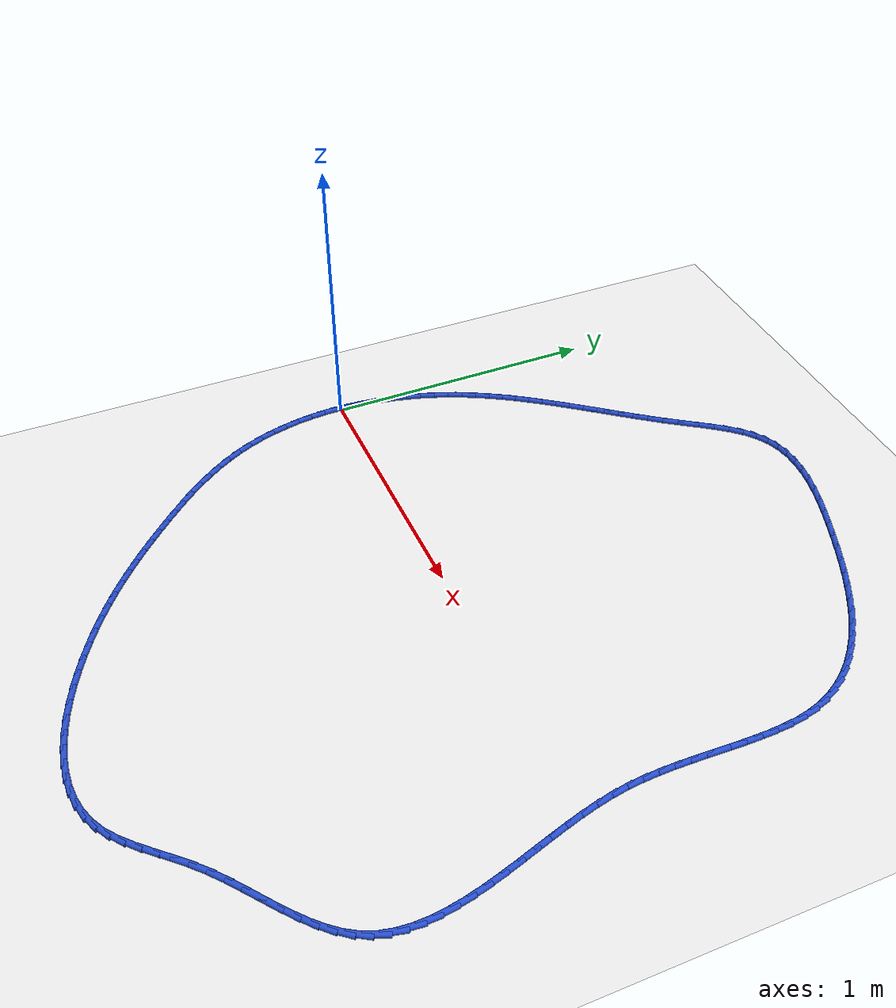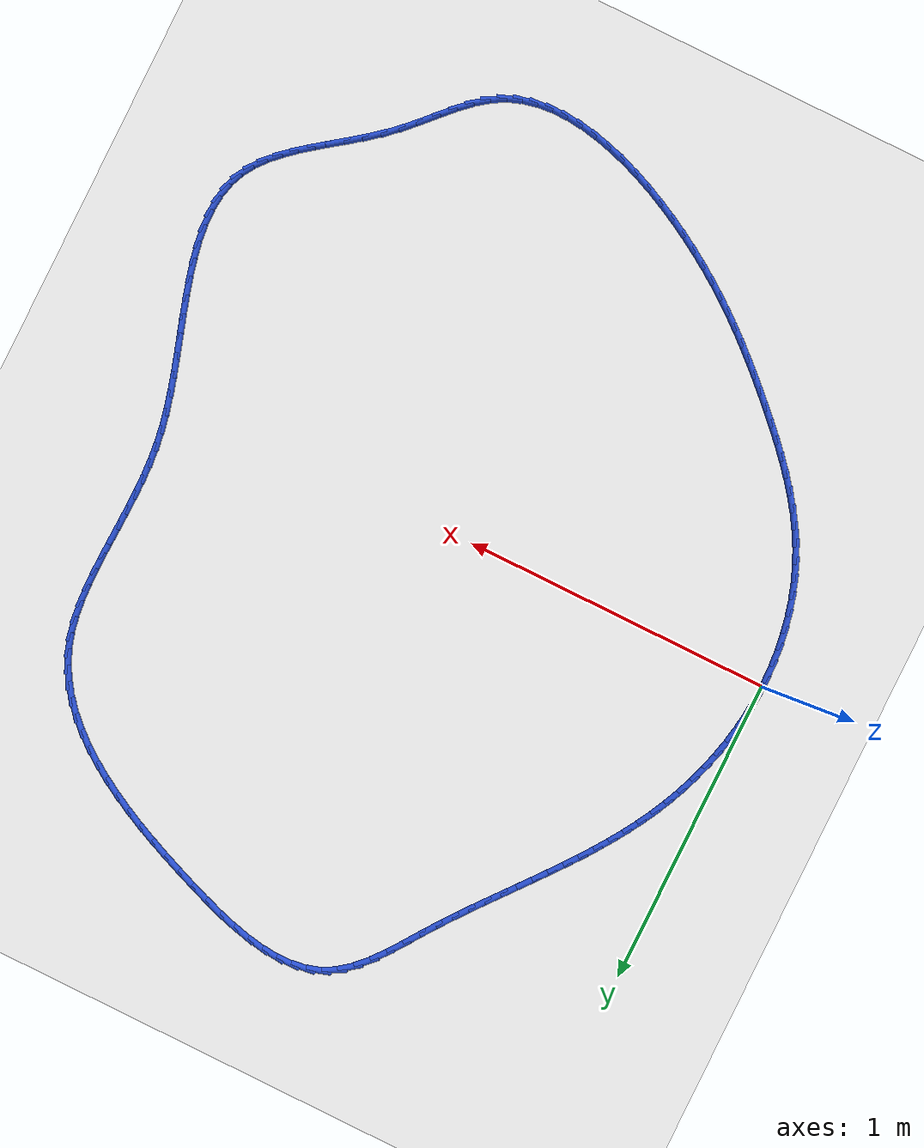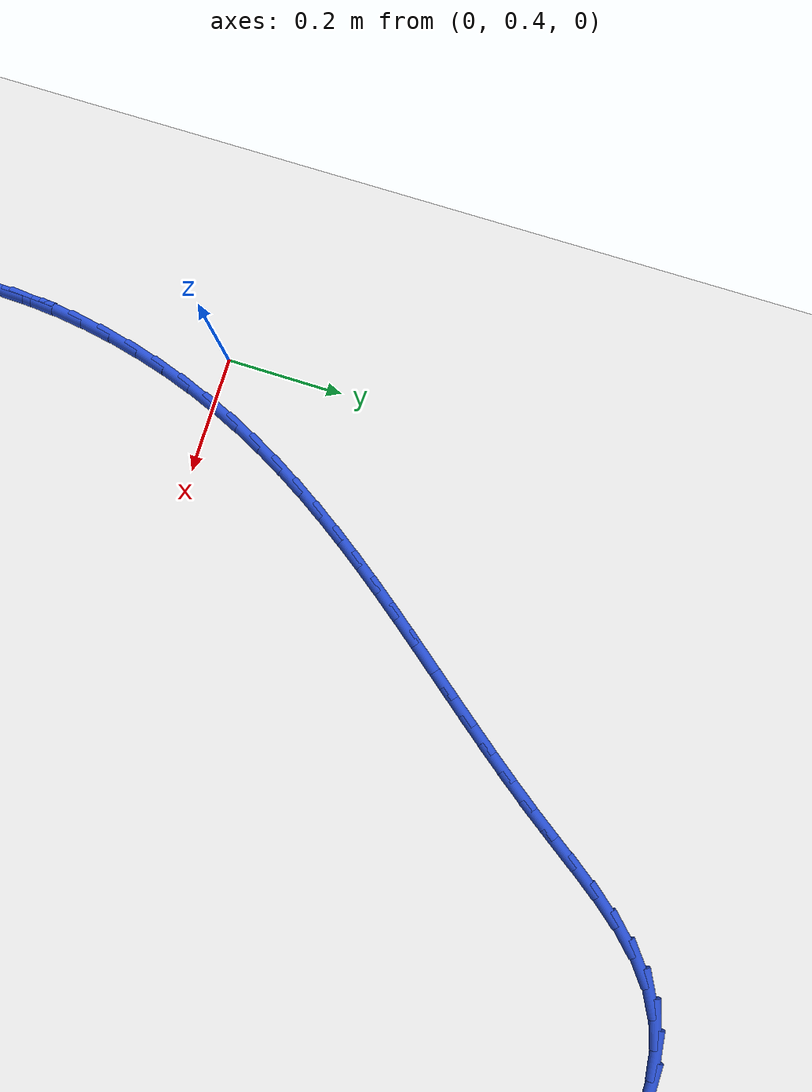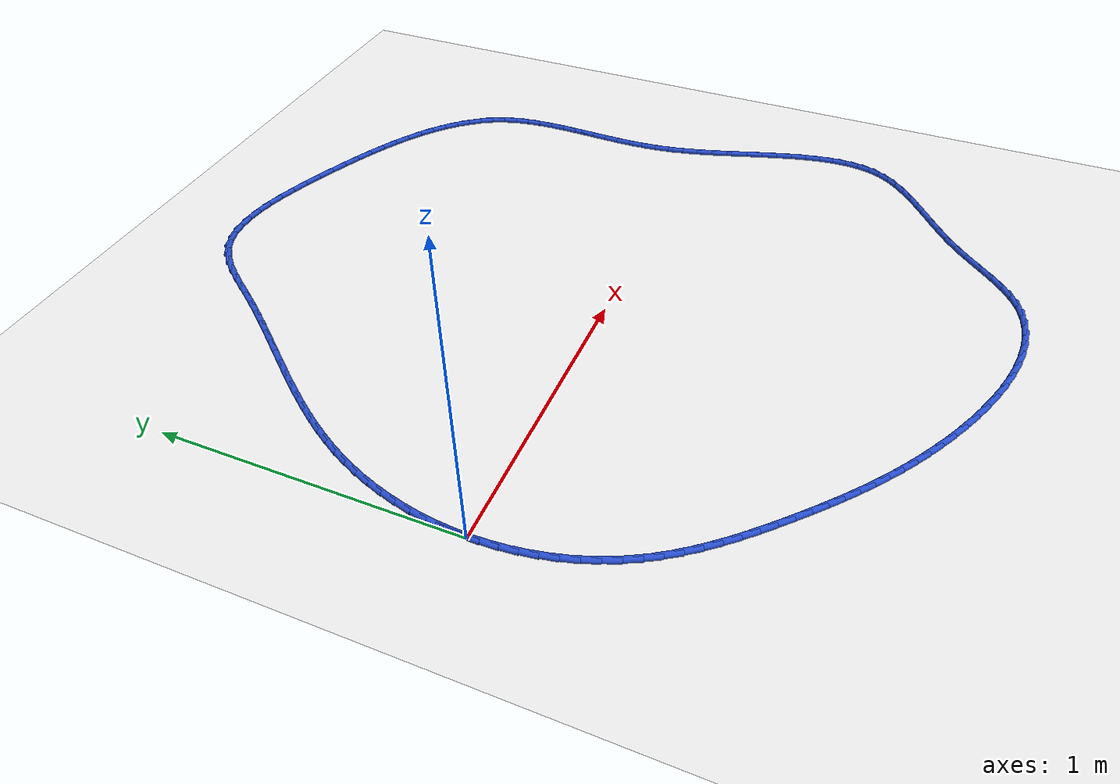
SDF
<sdf version="1.6">
 <world name="default">
  <light name="sun" type="directional">
   <pose>0 0 10 0 -0 0</pose>
   <diffuse>0.8 0.8 0.8 1</diffuse>
   <specular>0.2 0.2 0.2 1</specular>
   <attenuation>
    <range>1000</range>
    <constant>0.9</constant>
    <linear>0.01</linear>
    <quadratic>0.001</quadratic>
   </attenuation>
   <direction>-0.5 0.1 -0.9</direction>
  </light>
  <model name="ground_plane">
   <static>1</static>
   <link name="link">
    <collision name="collision">
     <geometry><plane><normal>0 0 1</normal><size>100 100</size></plane></geometry>
     <surface><friction><ode><mu>100</mu><mu2>50</mu2></ode></friction></surface>
    </collision>
    <visual name="visual">
     <cast_shadows>0</cast_shadows>
     <geometry><plane><normal>0 0 1</normal><size>100 100</size></plane></geometry>
     <material>
      <script><uri>file://media/materials/scripts/gazebo.material</uri><name>Gazebo/WhiteGlow</name></script>
     </material>
    </visual>
   </link>
  </model>
  <gravity>0 0 -9.8</gravity>
  <magnetic_field>6e-06 2.3e-05 -4.2e-05</magnetic_field>
  <atmosphere type="adiabatic"/>
  <physics name="default_physics" default="0" type="ode">
   <max_step_size>0.001</max_step_size>
   <real_time_factor>1</real_time_factor>
   <real_time_update_rate>1000</real_time_update_rate>
  </physics>
  <scene><ambient>0.4 0.4 0.4 1</ambient><background>0.7 0.7 0.7 1</background><shadows>1</shadows></scene>
  <spherical_coordinates>
   <surface_model>EARTH_WGS84</surface_model>
   <latitude_deg>0</latitude_deg>
   <longitude_deg>0</longitude_deg>
   <elevation>0</elevation>
   <heading_deg>0</heading_deg>
  </spherical_coordinates>
  <model name="line">
   <link name="link_0">
    <pose>-4.5102810375396984e-17 1.8041124150158794e-16 0.01 0 1.57 1.5296454746573978</pose>
    <collision name="collision">
     <geometry><cylinder><radius>0.01</radius><length>0.08</length></cylinder></geometry>
    </collision>
    <visual name="visual">
     <material>
      <script><name>Gazebo/Blue</name><uri>file://media/materials/scripts/gazebo.material</uri></script>
     </material>
     <geometry><cylinder><radius>0.01</radius><length>0.08</length></cylinder></geometry>
    </visual>
   </link>
   <link name="link_1">
    <pose>0.0022390424568003026 0.054379881303228794 0.01 0 1.57 1.4760865553160318</pose>
    <collision name="collision">
     <geometry><cylinder><radius>0.01</radius><length>0.08</length></cylinder></geometry>
    </collision>
    <visual name="visual">
     <material>
      <script><name>Gazebo/Blue</name><uri>file://media/materials/scripts/gazebo.material</uri></script>
     </material>
     <geometry><cylinder><radius>0.01</radius><length>0.08</length></cylinder></geometry>
    </visual>
   </link>
   <link name="link_2">
    <pose>0.007383099265475225 0.10853128400224349 0.01 0 1.57 1.4243346467549942</pose>
    <collision name="collision">
     <geometry><cylinder><radius>0.01</radius><length>0.08</length></cylinder></geometry>
    </collision>
    <visual name="visual">
     <material>
      <script><name>Gazebo/Blue</name><uri>file://media/materials/scripts/gazebo.material</uri></script>
     </material>
     <geometry><cylinder><radius>0.01</radius><length>0.08</length></cylinder></geometry>
    </visual>
   </link>
   <link name="link_3">
    <pose>0.01531320017357622 0.16228812144478444 0.01 0 1.57 1.3741611731956764</pose>
    <collision name="collision">
     <geometry><cylinder><radius>0.01</radius><length>0.08</length></cylinder></geometry>
    </collision>
    <visual name="visual">
     <material>
      <script><name>Gazebo/Blue</name><uri>file://media/materials/scripts/gazebo.material</uri></script>
     </material>
     <geometry><cylinder><radius>0.01</radius><length>0.08</length></cylinder></geometry>
    </visual>
   </link>
   <link name="link_4">
    <pose>0.02591037492865475 0.21548430697859156 0.01 0 1.57 1.3253169691965252</pose>
    <collision name="collision">
     <geometry><cylinder><radius>0.01</radius><length>0.08</length></cylinder></geometry>
    </collision>
    <visual name="visual">
     <material>
      <script><name>Gazebo/Blue</name><uri>file://media/materials/scripts/gazebo.material</uri></script>
     </material>
     <geometry><cylinder><radius>0.01</radius><length>0.08</length></cylinder></geometry>
    </visual>
   </link>
   <link name="link_5">
    <pose>0.03905565327826232 0.267953753951405 0.01 0 1.57 1.2775363864372953</pose>
    <collision name="collision">
     <geometry><cylinder><radius>0.01</radius><length>0.08</length></cylinder></geometry>
    </collision>
    <visual name="visual">
     <material>
      <script><name>Gazebo/Blue</name><uri>file://media/materials/scripts/gazebo.material</uri></script>
     </material>
     <geometry><cylinder><radius>0.01</radius><length>0.08</length></cylinder></geometry>
    </visual>
   </link>
   <link name="link_6">
    <pose>0.05463006496995043 0.319530375710965 0.01 0 1.57 1.230539522901242</pose>
    <collision name="collision">
     <geometry><cylinder><radius>0.01</radius><length>0.08</length></cylinder></geometry>
    </collision>
    <visual name="visual">
     <material>
      <script><name>Gazebo/Blue</name><uri>file://media/materials/scripts/gazebo.material</uri></script>
     </material>
     <geometry><cylinder><radius>0.01</radius><length>0.08</length></cylinder></geometry>
    </visual>
   </link>
   <link name="link_7">
    <pose>0.07251463975127054 0.37004808560501146 0.01 0 1.57 1.1840328055751552</pose>
    <collision name="collision">
     <geometry><cylinder><radius>0.01</radius><length>0.08</length></cylinder></geometry>
    </collision>
    <visual name="visual">
     <material>
      <script><name>Gazebo/Blue</name><uri>file://media/materials/scripts/gazebo.material</uri></script>
     </material>
     <geometry><cylinder><radius>0.01</radius><length>0.08</length></cylinder></geometry>
    </visual>
   </link>
   <link name="link_8">
    <pose>0.09259040736977417 0.4193407969812844 0.01 0 1.57 1.1379035304697056</pose>
    <collision name="collision">
     <geometry><cylinder><radius>0.01</radius><length>0.08</length></cylinder></geometry>
    </collision>
    <visual name="visual">
     <material>
      <script><name>Gazebo/Blue</name><uri>file://media/materials/scripts/gazebo.material</uri></script>
     </material>
     <geometry><cylinder><radius>0.01</radius><length>0.08</length></cylinder></geometry>
    </visual>
   </link>
   <link name="link_9">
    <pose>0.11473577889846497 0.46726133566953015 0.01 0 1.57 1.0940509659782551</pose>
    <collision name="collision">
     <geometry><cylinder><radius>0.01</radius><length>0.08</length></cylinder></geometry>
    </collision>
    <visual name="visual">
     <material>
      <script><name>Gazebo/Blue</name><uri>file://media/materials/scripts/gazebo.material</uri></script>
     </material>
     <geometry><cylinder><radius>0.01</radius><length>0.08</length></cylinder></geometry>
    </visual>
   </link>
   <link name="link_10">
    <pose>0.1388020942412135 0.5138580397671618 0.01 0 1.57 1.0539960227331135</pose>
    <collision name="collision">
     <geometry><cylinder><radius>0.01</radius><length>0.08</length></cylinder></geometry>
    </collision>
    <visual name="visual">
     <material>
      <script><name>Gazebo/Blue</name><uri>file://media/materials/scripts/gazebo.material</uri></script>
     </material>
     <geometry><cylinder><radius>0.01</radius><length>0.08</length></cylinder></geometry>
    </visual>
   </link>
   <link name="link_11">
    <pose>0.16462470592113299 0.559294710765527 0.01 0 1.57 1.0180784345199974</pose>
    <collision name="collision">
     <geometry><cylinder><radius>0.01</radius><length>0.08</length></cylinder></geometry>
    </collision>
    <visual name="visual">
     <material>
      <script><name>Gazebo/Blue</name><uri>file://media/materials/scripts/gazebo.material</uri></script>
     </material>
     <geometry><cylinder><radius>0.01</radius><length>0.08</length></cylinder></geometry>
    </visual>
   </link>
   <link name="link_12">
    <pose>0.19203875917318564 0.6037366472238043 0.01 0 1.57 0.986523205857931</pose>
    <collision name="collision">
     <geometry><cylinder><radius>0.01</radius><length>0.08</length></cylinder></geometry>
    </collision>
    <visual name="visual">
     <material>
      <script><name>Gazebo/Blue</name><uri>file://media/materials/scripts/gazebo.material</uri></script>
     </material>
     <geometry><cylinder><radius>0.01</radius><length>0.08</length></cylinder></geometry>
    </visual>
   </link>
   <link name="link_13">
    <pose>0.22087939923233366 0.647349147701173 0.01 0 1.57 0.959468707556324</pose>
    <collision name="collision">
     <geometry><cylinder><radius>0.01</radius><length>0.08</length></cylinder></geometry>
    </collision>
    <visual name="visual">
     <material>
      <script><name>Gazebo/Blue</name><uri>file://media/materials/scripts/gazebo.material</uri></script>
     </material>
     <geometry><cylinder><radius>0.01</radius><length>0.08</length></cylinder></geometry>
    </visual>
   </link>
   <link name="link_14">
    <pose>0.25098177133353927 0.6902975107568113 0.01 0 1.57 0.9369821409539862</pose>
    <collision name="collision">
     <geometry><cylinder><radius>0.01</radius><length>0.08</length></cylinder></geometry>
    </collision>
    <visual name="visual">
     <material>
      <script><name>Gazebo/Blue</name><uri>file://media/materials/scripts/gazebo.material</uri></script>
     </material>
     <geometry><cylinder><radius>0.01</radius><length>0.08</length></cylinder></geometry>
    </visual>
   </link>
   <link name="link_15">
    <pose>0.2821810207117648 0.7327470349498988 0.01 0 1.57 0.9190753835880875</pose>
    <collision name="collision">
     <geometry><cylinder><radius>0.01</radius><length>0.08</length></cylinder></geometry>
    </collision>
    <visual name="visual">
     <material>
      <script><name>Gazebo/Blue</name><uri>file://media/materials/scripts/gazebo.material</uri></script>
     </material>
     <geometry><cylinder><radius>0.01</radius><length>0.08</length></cylinder></geometry>
    </visual>
   </link>
   <link name="link_16">
    <pose>0.31431229260197247 0.7748630188396135 0.01 0 1.57 0.9057194745621432</pose>
    <collision name="collision">
     <geometry><cylinder><radius>0.01</radius><length>0.08</length></cylinder></geometry>
    </collision>
    <visual name="visual">
     <material>
      <script><name>Gazebo/Blue</name><uri>file://media/materials/scripts/gazebo.material</uri></script>
     </material>
     <geometry><cylinder><radius>0.01</radius><length>0.08</length></cylinder></geometry>
    </visual>
   </link>
   <link name="link_17">
    <pose>0.3472107322391245 0.816810760985135 0.01 0 1.57 0.8968566969022087</pose>
    <collision name="collision">
     <geometry><cylinder><radius>0.01</radius><length>0.08</length></cylinder></geometry>
    </collision>
    <visual name="visual">
     <material>
      <script><name>Gazebo/Blue</name><uri>file://media/materials/scripts/gazebo.material</uri></script>
     </material>
     <geometry><cylinder><radius>0.01</radius><length>0.08</length></cylinder></geometry>
    </visual>
   </link>
   <link name="link_18">
    <pose>0.3807114848581831 0.8587555599456416 0.01 0 1.57 0.8924097803168987</pose>
    <collision name="collision">
     <geometry><cylinder><radius>0.01</radius><length>0.08</length></cylinder></geometry>
    </collision>
    <visual name="visual">
     <material>
      <script><name>Gazebo/Blue</name><uri>file://media/materials/scripts/gazebo.material</uri></script>
     </material>
     <geometry><cylinder><radius>0.01</radius><length>0.08</length></cylinder></geometry>
    </visual>
   </link>
   <link name="link_19">
    <pose>0.4146496956941105 0.9008627142803124 0.01 0 1.57 0.8922881439437028</pose>
    <collision name="collision">
     <geometry><cylinder><radius>0.01</radius><length>0.08</length></cylinder></geometry>
    </collision>
    <visual name="visual">
     <material>
      <script><name>Gazebo/Blue</name><uri>file://media/materials/scripts/gazebo.material</uri></script>
     </material>
     <geometry><cylinder><radius>0.01</radius><length>0.08</length></cylinder></geometry>
    </visual>
   </link>
   <link name="link_20">
    <pose>0.4488605099818691 0.9432975225483262 0.01 0 1.57 0.8963913430219269</pose>
    <collision name="collision">
     <geometry><cylinder><radius>0.01</radius><length>0.08</length></cylinder></geometry>
    </collision>
    <visual name="visual">
     <material>
      <script><name>Gazebo/Blue</name><uri>file://media/materials/scripts/gazebo.material</uri></script>
     </material>
     <geometry><cylinder><radius>0.01</radius><length>0.08</length></cylinder></geometry>
    </visual>
   </link>
   <link name="link_21">
    <pose>0.4831790729564208 0.9862252833088612 0.01 0 1.57 0.9046100182879823</pose>
    <collision name="collision">
     <geometry><cylinder><radius>0.01</radius><length>0.08</length></cylinder></geometry>
    </collision>
    <visual name="visual">
     <material>
      <script><name>Gazebo/Blue</name><uri>file://media/materials/scripts/gazebo.material</uri></script>
     </material>
     <geometry><cylinder><radius>0.01</radius><length>0.08</length></cylinder></geometry>
    </visual>
   </link>
   <link name="link_22">
    <pose>0.5174405298527281 1.029811295121097 0.01 0 1.57 0.9168247179570859</pose>
    <collision name="collision">
     <geometry><cylinder><radius>0.01</radius><length>0.08</length></cylinder></geometry>
    </collision>
    <visual name="visual">
     <material>
      <script><name>Gazebo/Blue</name><uri>file://media/materials/scripts/gazebo.material</uri></script>
     </material>
     <geometry><cylinder><radius>0.01</radius><length>0.08</length></cylinder></geometry>
    </visual>
   </link>
   <link name="link_23">
    <pose>0.5514800259057534 1.0742208565442124 0.01 0 1.57 0.9329030076732835</pose>
    <collision name="collision">
     <geometry><cylinder><radius>0.01</radius><length>0.08</length></cylinder></geometry>
    </collision>
    <visual name="visual">
     <material>
      <script><name>Gazebo/Blue</name><uri>file://media/materials/scripts/gazebo.material</uri></script>
     </material>
     <geometry><cylinder><radius>0.01</radius><length>0.08</length></cylinder></geometry>
    </visual>
   </link>
   <link name="link_24">
    <pose>0.5851327063504586 1.1196192661373858 0.01 0 1.57 0.9513599960890838</pose>
    <collision name="collision">
     <geometry><cylinder><radius>0.01</radius><length>0.08</length></cylinder></geometry>
    </collision>
    <visual name="visual">
     <material>
      <script><name>Gazebo/Blue</name><uri>file://media/materials/scripts/gazebo.material</uri></script>
     </material>
     <geometry><cylinder><radius>0.01</radius><length>0.08</length></cylinder></geometry>
    </visual>
   </link>
   <link name="link_25">
    <pose>0.6182712246254696 1.1660930450590108 0.01 0 1.57 0.9546941731813836</pose>
    <collision name="collision">
     <geometry><cylinder><radius>0.01</radius><length>0.08</length></cylinder></geometry>
    </collision>
    <visual name="visual">
     <material>
      <script><name>Gazebo/Blue</name><uri>file://media/materials/scripts/gazebo.material</uri></script>
     </material>
     <geometry><cylinder><radius>0.01</radius><length>0.08</length></cylinder></geometry>
    </visual>
   </link>
   <link name="link_26">
    <pose>0.6512631888355103 1.2126891754255185 0.01 0 1.57 0.9302929567576277</pose>
    <collision name="collision">
     <geometry><cylinder><radius>0.01</radius><length>0.08</length></cylinder></geometry>
    </collision>
    <visual name="visual">
     <material>
      <script><name>Gazebo/Blue</name><uri>file://media/materials/scripts/gazebo.material</uri></script>
     </material>
     <geometry><cylinder><radius>0.01</radius><length>0.08</length></cylinder></geometry>
    </visual>
   </link>
   <link name="link_27">
    <pose>0.6848259382244212 1.2577201091060215 0.01 0 1.57 0.8752677764476182</pose>
    <collision name="collision">
     <geometry><cylinder><radius>0.01</radius><length>0.08</length></cylinder></geometry>
    </collision>
    <visual name="visual">
     <material>
      <script><name>Gazebo/Blue</name><uri>file://media/materials/scripts/gazebo.material</uri></script>
     </material>
     <geometry><cylinder><radius>0.01</radius><length>0.08</length></cylinder></geometry>
    </visual>
   </link>
   <link name="link_28">
    <pose>0.719684172846758 1.2994828382707098 0.01 0 1.57 0.7842185363364818</pose>
    <collision name="collision">
     <geometry><cylinder><radius>0.01</radius><length>0.08</length></cylinder></geometry>
    </collision>
    <visual name="visual">
     <material>
      <script><name>Gazebo/Blue</name><uri>file://media/materials/scripts/gazebo.material</uri></script>
     </material>
     <geometry><cylinder><radius>0.01</radius><length>0.08</length></cylinder></geometry>
    </visual>
   </link>
   <link name="link_29">
    <pose>0.7565625927570755 1.3362743550897724 0.01 0 1.57 0.6499277924118434</pose>
    <collision name="collision">
     <geometry><cylinder><radius>0.01</radius><length>0.08</length></cylinder></geometry>
    </collision>
    <visual name="visual">
     <material>
      <script><name>Gazebo/Blue</name><uri>file://media/materials/scripts/gazebo.material</uri></script>
     </material>
     <geometry><cylinder><radius>0.01</radius><length>0.08</length></cylinder></geometry>
    </visual>
   </link>
   <link name="link_30">
    <pose>0.7961858980099293 1.3663916517333994 0.01 0 1.57 0.47115376710419815</pose>
    <collision name="collision">
     <geometry><cylinder><radius>0.01</radius><length>0.08</length></cylinder></geometry>
    </collision>
    <visual name="visual">
     <material>
      <script><name>Gazebo/Blue</name><uri>file://media/materials/scripts/gazebo.material</uri></script>
     </material>
     <geometry><cylinder><radius>0.01</radius><length>0.08</length></cylinder></geometry>
    </visual>
   </link>
   <link name="link_31">
    <pose>0.8392011386602475 1.3883043991376236 0.01 0 1.57 0.28782883131402026</pose>
    <collision name="collision">
     <geometry><cylinder><radius>0.01</radius><length>0.08</length></cylinder></geometry>
    </collision>
    <visual name="visual">
     <material>
      <script><name>Gazebo/Blue</name><uri>file://media/materials/scripts/gazebo.material</uri></script>
     </material>
     <geometry><cylinder><radius>0.01</radius><length>0.08</length></cylinder></geometry>
    </visual>
   </link>
   <link name="link_32">
    <pose>0.8855598792674302 1.4020288951233262 0.01 0 1.57 0.12848597164306225</pose>
    <collision name="collision">
     <geometry><cylinder><radius>0.01</radius><length>0.08</length></cylinder></geometry>
    </collision>
    <visual name="visual">
     <material>
      <script><name>Gazebo/Blue</name><uri>file://media/materials/scripts/gazebo.material</uri></script>
     </material>
     <geometry><cylinder><radius>0.01</radius><length>0.08</length></cylinder></geometry>
    </visual>
   </link>
   <link name="link_33">
    <pose>0.9348470828918742 1.4083966892140172 0.01 0 1.57 -0.002896581844115343</pose>
    <collision name="collision">
     <geometry><cylinder><radius>0.01</radius><length>0.08</length></cylinder></geometry>
    </collision>
    <visual name="visual">
     <material>
      <script><name>Gazebo/Blue</name><uri>file://media/materials/scripts/gazebo.material</uri></script>
     </material>
     <geometry><cylinder><radius>0.01</radius><length>0.08</length></cylinder></geometry>
    </visual>
   </link>
   <link name="link_34">
    <pose>0.9866444197591359 1.4082466535688647 0.01 0 1.57 -0.10774746901296946</pose>
    <collision name="collision">
     <geometry><cylinder><radius>0.01</radius><length>0.08</length></cylinder></geometry>
    </collision>
    <visual name="visual">
     <material>
      <script><name>Gazebo/Blue</name><uri>file://media/materials/scripts/gazebo.material</uri></script>
     </material>
     <geometry><cylinder><radius>0.01</radius><length>0.08</length></cylinder></geometry>
    </visual>
   </link>
   <link name="link_35">
    <pose>1.0405335600947718 1.4024176603470386 0.01 0 1.57 -0.18970989477356984</pose>
    <collision name="collision">
     <geometry><cylinder><radius>0.01</radius><length>0.08</length></cylinder></geometry>
    </collision>
    <visual name="visual">
     <material>
      <script><name>Gazebo/Blue</name><uri>file://media/materials/scripts/gazebo.material</uri></script>
     </material>
     <geometry><cylinder><radius>0.01</radius><length>0.08</length></cylinder></geometry>
    </visual>
   </link>
   <link name="link_36">
    <pose>1.0960961741243385 1.3917485817077082 0.01 0 1.57 -0.2526804181186774</pose>
    <collision name="collision">
     <geometry><cylinder><radius>0.01</radius><length>0.08</length></cylinder></geometry>
    </collision>
    <visual name="visual">
     <material>
      <script><name>Gazebo/Blue</name><uri>file://media/materials/scripts/gazebo.material</uri></script>
     </material>
     <geometry><cylinder><radius>0.01</radius><length>0.08</length></cylinder></geometry>
    </visual>
   </link>
   <link name="link_37">
    <pose>1.1529139320733928 1.377078289810043 0.01 0 1.57 -0.2999680848438112</pose>
    <collision name="collision">
     <geometry><cylinder><radius>0.01</radius><length>0.08</length></cylinder></geometry>
    </collision>
    <visual name="visual">
     <material>
      <script><name>Gazebo/Blue</name><uri>file://media/materials/scripts/gazebo.material</uri></script>
     </material>
     <geometry><cylinder><radius>0.01</radius><length>0.08</length></cylinder></geometry>
    </visual>
   </link>
   <link name="link_38">
    <pose>1.210568504167491 1.359245656813213 0.01 0 1.57 -0.33407273972191776</pose>
    <collision name="collision">
     <geometry><cylinder><radius>0.01</radius><length>0.08</length></cylinder></geometry>
    </collision>
    <visual name="visual">
     <material>
      <script><name>Gazebo/Blue</name><uri>file://media/materials/scripts/gazebo.material</uri></script>
     </material>
     <geometry><cylinder><radius>0.01</radius><length>0.08</length></cylinder></geometry>
    </visual>
   </link>
   <link name="link_39">
    <pose>1.2686415606321901 1.3390895548763873 0.01 0 1.57 -0.3567050726452201</pose>
    <collision name="collision">
     <geometry><cylinder><radius>0.01</radius><length>0.08</length></cylinder></geometry>
    </collision>
    <visual name="visual">
     <material>
      <script><name>Gazebo/Blue</name><uri>file://media/materials/scripts/gazebo.material</uri></script>
     </material>
     <geometry><cylinder><radius>0.01</radius><length>0.08</length></cylinder></geometry>
    </visual>
   </link>
   <link name="link_40">
    <pose>1.3267147757637379 1.3174488181871438 0.01 0 1.57 -0.3716649266323783</pose>
    <collision name="collision">
     <geometry><cylinder><radius>0.01</radius><length>0.08</length></cylinder></geometry>
    </collision>
    <visual name="visual">
     <material>
      <script><name>Gazebo/Blue</name><uri>file://media/materials/scripts/gazebo.material</uri></script>
     </material>
     <geometry><cylinder><radius>0.01</radius><length>0.08</length></cylinder></geometry>
    </visual>
   </link>
   <link name="link_41">
    <pose>1.3843906596289903 1.2949679239570293 0.01 0 1.57 -0.38870124824013785</pose>
    <collision name="collision">
     <geometry><cylinder><radius>0.01</radius><length>0.08</length></cylinder></geometry>
    </collision>
    <visual name="visual">
     <material>
      <script><name>Gazebo/Blue</name><uri>file://media/materials/scripts/gazebo.material</uri></script>
     </material>
     <geometry><cylinder><radius>0.01</radius><length>0.08</length></cylinder></geometry>
    </visual>
   </link>
   <link name="link_42">
    <pose>1.441341056239885 1.2716445993369665 0.01 0 1.57 -0.4100248646708028</pose>
    <collision name="collision">
     <geometry><cylinder><radius>0.01</radius><length>0.08</length></cylinder></geometry>
    </collision>
    <visual name="visual">
     <material>
      <script><name>Gazebo/Blue</name><uri>file://media/materials/scripts/gazebo.material</uri></script>
     </material>
     <geometry><cylinder><radius>0.01</radius><length>0.08</length></cylinder></geometry>
    </visual>
   </link>
   <link name="link_43">
    <pose>1.497252213330228 1.2473422129327394 0.01 0 1.57 -0.4359888340937455</pose>
    <collision name="collision">
     <geometry><cylinder><radius>0.01</radius><length>0.08</length></cylinder></geometry>
    </collision>
    <visual name="visual">
     <material>
      <script><name>Gazebo/Blue</name><uri>file://media/materials/scripts/gazebo.material</uri></script>
     </material>
     <geometry><cylinder><radius>0.01</radius><length>0.08</length></cylinder></geometry>
    </visual>
   </link>
   <link name="link_44">
    <pose>1.551810378633825 1.2219241333501318 0.01 0 1.57 -0.46704039360065797</pose>
    <collision name="collision">
     <geometry><cylinder><radius>0.01</radius><length>0.08</length></cylinder></geometry>
    </collision>
    <visual name="visual">
     <material>
      <script><name>Gazebo/Blue</name><uri>file://media/materials/scripts/gazebo.material</uri></script>
     </material>
     <geometry><cylinder><radius>0.01</radius><length>0.08</length></cylinder></geometry>
    </visual>
   </link>
   <link name="link_45">
    <pose>1.6047017998844797 1.1952537291949275 0.01 0 1.57 -0.5037227444229363</pose>
    <collision name="collision">
     <geometry><cylinder><radius>0.01</radius><length>0.08</length></cylinder></geometry>
    </collision>
    <visual name="visual">
     <material>
      <script><name>Gazebo/Blue</name><uri>file://media/materials/scripts/gazebo.material</uri></script>
     </material>
     <geometry><cylinder><radius>0.01</radius><length>0.08</length></cylinder></geometry>
    </visual>
   </link>
   <link name="link_46">
    <pose>1.6556127248159982 1.1671943690729105 0.01 0 1.57 -0.5466715869590618</pose>
    <collision name="collision">
     <geometry><cylinder><radius>0.01</radius><length>0.08</length></cylinder></geometry>
    </collision>
    <visual name="visual">
     <material>
      <script><name>Gazebo/Blue</name><uri>file://media/materials/scripts/gazebo.material</uri></script>
     </material>
     <geometry><cylinder><radius>0.01</radius><length>0.08</length></cylinder></geometry>
    </visual>
   </link>
   <link name="link_47">
    <pose>1.7042294011621848 1.1376094215898649 0.01 0 1.57 -0.5966007590990389</pose>
    <collision name="collision">
     <geometry><cylinder><radius>0.01</radius><length>0.08</length></cylinder></geometry>
    </collision>
    <visual name="visual">
     <material>
      <script><name>Gazebo/Blue</name><uri>file://media/materials/scripts/gazebo.material</uri></script>
     </material>
     <geometry><cylinder><radius>0.01</radius><length>0.08</length></cylinder></geometry>
    </visual>
   </link>
   <link name="link_48">
    <pose>1.7502380766568466 1.1063622553515746 0.01 0 1.57 -0.6542684716082908</pose>
    <collision name="collision">
     <geometry><cylinder><radius>0.01</radius><length>0.08</length></cylinder></geometry>
    </collision>
    <visual name="visual">
     <material>
      <script><name>Gazebo/Blue</name><uri>file://media/materials/scripts/gazebo.material</uri></script>
     </material>
     <geometry><cylinder><radius>0.01</radius><length>0.08</length></cylinder></geometry>
    </visual>
   </link>
   <link name="link_49">
    <pose>1.7933249990337863 1.0733162389638236 0.01 0 1.57 -0.7204125657458925</pose>
    <collision name="collision">
     <geometry><cylinder><radius>0.01</radius><length>0.08</length></cylinder></geometry>
    </collision>
    <visual name="visual">
     <material>
      <script><name>Gazebo/Blue</name><uri>file://media/materials/scripts/gazebo.material</uri></script>
     </material>
     <geometry><cylinder><radius>0.01</radius><length>0.08</length></cylinder></geometry>
    </visual>
   </link>
   <link name="link_50">
    <pose>1.8331764160268111 1.0383347410323962 0.01 0 1.57 -0.7956417371555586</pose>
    <collision name="collision">
     <geometry><cylinder><radius>0.01</radius><length>0.08</length></cylinder></geometry>
    </collision>
    <visual name="visual">
     <material>
      <script><name>Gazebo/Blue</name><uri>file://media/materials/scripts/gazebo.material</uri></script>
     </material>
     <geometry><cylinder><radius>0.01</radius><length>0.08</length></cylinder></geometry>
    </visual>
   </link>
   <link name="link_51">
    <pose>1.869478575369725 1.0012811301630757 0.01 0 1.57 -0.8802737280664794</pose>
    <collision name="collision">
     <geometry><cylinder><radius>0.01</radius><length>0.08</length></cylinder></geometry>
    </collision>
    <visual name="visual">
     <material>
      <script><name>Gazebo/Blue</name><uri>file://media/materials/scripts/gazebo.material</uri></script>
     </material>
     <geometry><cylinder><radius>0.01</radius><length>0.08</length></cylinder></geometry>
    </visual>
   </link>
   <link name="link_52">
    <pose>1.9019177247963333 0.9620187749616462 0.01 0 1.57 -0.9741271771004304</pose>
    <collision name="collision">
     <geometry><cylinder><radius>0.01</radius><length>0.08</length></cylinder></geometry>
    </collision>
    <visual name="visual">
     <material>
      <script><name>Gazebo/Blue</name><uri>file://media/materials/scripts/gazebo.material</uri></script>
     </material>
     <geometry><cylinder><radius>0.01</radius><length>0.08</length></cylinder></geometry>
    </visual>
   </link>
   <link name="link_53">
    <pose>1.930180112040441 0.9204110440338923 0.01 0 1.57 -1.0763057466797155</pose>
    <collision name="collision">
     <geometry><cylinder><radius>0.01</radius><length>0.08</length></cylinder></geometry>
    </collision>
    <visual name="visual">
     <material>
      <script><name>Gazebo/Blue</name><uri>file://media/materials/scripts/gazebo.material</uri></script>
     </material>
     <geometry><cylinder><radius>0.01</radius><length>0.08</length></cylinder></geometry>
    </visual>
   </link>
   <link name="link_54">
    <pose>1.9539519848358542 0.8763213059855977 0.01 0 1.57 -1.1850546487388498</pose>
    <collision name="collision">
     <geometry><cylinder><radius>0.01</radius><length>0.08</length></cylinder></geometry>
    </collision>
    <visual name="visual">
     <material>
      <script><name>Gazebo/Blue</name><uri>file://media/materials/scripts/gazebo.material</uri></script>
     </material>
     <geometry><cylinder><radius>0.01</radius><length>0.08</length></cylinder></geometry>
    </visual>
   </link>
   <link name="link_55">
    <pose>1.9729195909163768 0.8296129294225454 0.01 0 1.57 -1.2971792307961592</pose>
    <collision name="collision">
     <geometry><cylinder><radius>0.01</radius><length>0.08</length></cylinder></geometry>
    </collision>
    <visual name="visual">
     <material>
      <script><name>Gazebo/Blue</name><uri>file://media/materials/scripts/gazebo.material</uri></script>
     </material>
     <geometry><cylinder><radius>0.01</radius><length>0.08</length></cylinder></geometry>
    </visual>
   </link>
   <link name="link_56">
    <pose>1.9867963676709721 0.7801688885744567 0.01 0 1.57 -1.3974140076883164</pose>
    <collision name="collision">
     <geometry><cylinder><radius>0.01</radius><length>0.08</length></cylinder></geometry>
    </collision>
    <visual name="visual">
     <material>
      <script><name>Gazebo/Blue</name><uri>file://media/materials/scripts/gazebo.material</uri></script>
     </material>
     <geometry><cylinder><radius>0.01</radius><length>0.08</length></cylinder></geometry>
    </visual>
   </link>
   <link name="link_57">
    <pose>1.9958816667669042 0.7282946424334583 0.01 0 1.57 -1.4748461359365306</pose>
    <collision name="collision">
     <geometry><cylinder><radius>0.01</radius><length>0.08</length></cylinder></geometry>
    </collision>
    <visual name="visual">
     <material>
      <script><name>Gazebo/Blue</name><uri>file://media/materials/scripts/gazebo.material</uri></script>
     </material>
     <geometry><cylinder><radius>0.01</radius><length>0.08</length></cylinder></geometry>
    </visual>
   </link>
   <link name="link_58">
    <pose>2.001039642159687 0.6747029115474996 0.01 0 1.57 -1.532014505819472</pose>
    <collision name="collision">
     <geometry><cylinder><radius>0.01</radius><length>0.08</length></cylinder></geometry>
    </collision>
    <visual name="visual">
     <material>
      <script><name>Gazebo/Blue</name><uri>file://media/materials/scripts/gazebo.material</uri></script>
     </material>
     <geometry><cylinder><radius>0.01</radius><length>0.08</length></cylinder></geometry>
    </visual>
   </link>
   <link name="link_59">
    <pose>2.003157413279319 0.6201229761617231 0.01 0 1.57 1.5701523725100925</pose>
    <collision name="collision">
     <geometry><cylinder><radius>0.01</radius><length>0.08</length></cylinder></geometry>
    </collision>
    <visual name="visual">
     <material>
      <script><name>Gazebo/Blue</name><uri>file://media/materials/scripts/gazebo.material</uri></script>
     </material>
     <geometry><cylinder><radius>0.01</radius><length>0.08</length></cylinder></geometry>
    </visual>
   </link>
   <link name="link_60">
    <pose>2.0031220995557986 0.5652841165212736 0.01 0 1.57 1.546715828918001</pose>
    <collision name="collision">
     <geometry><cylinder><radius>0.01</radius><length>0.08</length></cylinder></geometry>
    </collision>
    <visual name="visual">
     <material>
      <script><name>Gazebo/Blue</name><uri>file://media/materials/scripts/gazebo.material</uri></script>
     </material>
     <geometry><cylinder><radius>0.01</radius><length>0.08</length></cylinder></geometry>
    </visual>
   </link>
   <link name="link_61">
    <pose>2.001812032090265 0.5108909623873911 0.01 0 1.57 1.5358651331182982</pose>
    <collision name="collision">
     <geometry><cylinder><radius>0.01</radius><length>0.08</length></cylinder></geometry>
    </collision>
    <visual name="visual">
     <material>
      <script><name>Gazebo/Blue</name><uri>file://media/materials/scripts/gazebo.material</uri></script>
     </material>
     <geometry><cylinder><radius>0.01</radius><length>0.08</length></cylinder></geometry>
    </visual>
   </link>
   <link name="link_62">
    <pose>1.9999346937156486 0.4571689292641732 0.01 0 1.57 1.5352837262179913</pose>
    <collision name="collision">
     <geometry><cylinder><radius>0.01</radius><length>0.08</length></cylinder></geometry>
    </collision>
    <visual name="visual">
     <material>
      <script><name>Gazebo/Blue</name><uri>file://media/materials/scripts/gazebo.material</uri></script>
     </material>
     <geometry><cylinder><radius>0.01</radius><length>0.08</length></cylinder></geometry>
    </visual>
   </link>
   <link name="link_63">
    <pose>1.9980424791554017 0.4039084242476523 0.01 0 1.57 1.5451472682016236</pose>
    <collision name="collision">
     <geometry><cylinder><radius>0.01</radius><length>0.08</length></cylinder></geometry>
    </collision>
    <visual name="visual">
     <material>
      <script><name>Gazebo/Blue</name><uri>file://media/materials/scripts/gazebo.material</uri></script>
     </material>
     <geometry><cylinder><radius>0.01</radius><length>0.08</length></cylinder></geometry>
    </visual>
   </link>
   <link name="link_64">
    <pose>1.9966821560941124 0.3508840710883387 0.01 0 1.57 1.5654833250983913</pose>
    <collision name="collision">
     <geometry><cylinder><radius>0.01</radius><length>0.08</length></cylinder></geometry>
    </collision>
    <visual name="visual">
     <material>
      <script><name>Gazebo/Blue</name><uri>file://media/materials/scripts/gazebo.material</uri></script>
     </material>
     <geometry><cylinder><radius>0.01</radius><length>0.08</length></cylinder></geometry>
    </visual>
   </link>
   <link name="link_65">
    <pose>1.9964004922163698 0.2978704935367421 0.01 0 1.57 -1.5455563566686896</pose>
    <collision name="collision">
     <geometry><cylinder><radius>0.01</radius><length>0.08</length></cylinder></geometry>
    </collision>
    <visual name="visual">
     <material>
      <script><name>Gazebo/Blue</name><uri>file://media/materials/scripts/gazebo.material</uri></script>
     </material>
     <geometry><cylinder><radius>0.01</radius><length>0.08</length></cylinder></geometry>
    </visual>
   </link>
   <link name="link_66">
    <pose>1.9977442552067624 0.24464231534337177 0.01 0 1.57 -1.5053768922109605</pose>
    <collision name="collision">
     <geometry><cylinder><radius>0.01</radius><length>0.08</length></cylinder></geometry>
    </collision>
    <visual name="visual">
     <material>
      <script><name>Gazebo/Blue</name><uri>file://media/materials/scripts/gazebo.material</uri></script>
     </material>
     <geometry><cylinder><radius>0.01</radius><length>0.08</length></cylinder></geometry>
    </visual>
   </link>
   <link name="link_67">
    <pose>2.001260212749877 0.19097416025873837 0.01 0 1.57 -1.456543324320946</pose>
    <collision name="collision">
     <geometry><cylinder><radius>0.01</radius><length>0.08</length></cylinder></geometry>
    </collision>
    <visual name="visual">
     <material>
      <script><name>Gazebo/Blue</name><uri>file://media/materials/scripts/gazebo.material</uri></script>
     </material>
     <geometry><cylinder><radius>0.01</radius><length>0.08</length></cylinder></geometry>
    </visual>
   </link>
   <link name="link_68">
    <pose>2.007495132530304 0.13664065203335085 0.01 0 1.57 -1.400907823950107</pose>
    <collision name="collision">
     <geometry><cylinder><radius>0.01</radius><length>0.08</length></cylinder></geometry>
    </collision>
    <visual name="visual">
     <material>
      <script><name>Gazebo/Blue</name><uri>file://media/materials/scripts/gazebo.material</uri></script>
     </material>
     <geometry><cylinder><radius>0.01</radius><length>0.08</length></cylinder></geometry>
    </visual>
   </link>
   <link name="link_69">
    <pose>2.016966521887778 0.08142742700411018 0.01 0 1.57 -1.3496364118905433</pose>
    <collision name="collision">
     <geometry><cylinder><radius>0.01</radius><length>0.08</length></cylinder></geometry>
    </collision>
    <visual name="visual">
     <material>
      <script><name>Gazebo/Blue</name><uri>file://media/materials/scripts/gazebo.material</uri></script>
     </material>
     <geometry><cylinder><radius>0.01</radius><length>0.08</length></cylinder></geometry>
    </visual>
   </link>
   <link name="link_70">
    <pose>2.0295742600240567 0.02535257547457161 0.01 0 1.57 -1.3112410905375973</pose>
    <collision name="collision">
     <geometry><cylinder><radius>0.01</radius><length>0.08</length></cylinder></geometry>
    </collision>
    <visual name="visual">
     <material>
      <script><name>Gazebo/Blue</name><uri>file://media/materials/scripts/gazebo.material</uri></script>
     </material>
     <geometry><cylinder><radius>0.01</radius><length>0.08</length></cylinder></geometry>
    </visual>
   </link>
   <link name="link_71">
    <pose>2.044629872431118 -0.03134437617193089 0.01 0 1.57 -1.2846464202993828</pose>
    <collision name="collision">
     <geometry><cylinder><radius>0.01</radius><length>0.08</length></cylinder></geometry>
    </collision>
    <visual name="visual">
     <material>
      <script><name>Gazebo/Blue</name><uri>file://media/materials/scripts/gazebo.material</uri></script>
     </material>
     <geometry><cylinder><radius>0.01</radius><length>0.08</length></cylinder></geometry>
    </visual>
   </link>
   <link name="link_72">
    <pose>2.061421483469755 -0.08841509417196947 0.01 0 1.57 -1.2688365653599714</pose>
    <collision name="collision">
     <geometry><cylinder><radius>0.01</radius><length>0.08</length></cylinder></geometry>
    </collision>
    <visual name="visual">
     <material>
      <script><name>Gazebo/Blue</name><uri>file://media/materials/scripts/gazebo.material</uri></script>
     </material>
     <geometry><cylinder><radius>0.01</radius><length>0.08</length></cylinder></geometry>
    </visual>
   </link>
   <link name="link_73">
    <pose>2.079237217500759 -0.14561124476211676 0.01 0 1.57 -1.2632478146298742</pose>
    <collision name="collision">
     <geometry><cylinder><radius>0.01</radius><length>0.08</length></cylinder></geometry>
    </collision>
    <visual name="visual">
     <material>
      <script><name>Gazebo/Blue</name><uri>file://media/materials/scripts/gazebo.material</uri></script>
     </material>
     <geometry><cylinder><radius>0.01</radius><length>0.08</length></cylinder></geometry>
    </visual>
   </link>
   <link name="link_74">
    <pose>2.097365198884924 -0.20268449417894266 0.01 0 1.57 -1.2677672863972622</pose>
    <collision name="collision">
     <geometry><cylinder><radius>0.01</radius><length>0.08</length></cylinder></geometry>
    </collision>
    <visual name="visual">
     <material>
      <script><name>Gazebo/Blue</name><uri>file://media/materials/scripts/gazebo.material</uri></script>
     </material>
     <geometry><cylinder><radius>0.01</radius><length>0.08</length></cylinder></geometry>
    </visual>
   </link>
   <link name="link_75">
    <pose>2.115093551983041 -0.25938650865901997 0.01 0 1.57 -1.2827436958456733</pose>
    <collision name="collision">
     <geometry><cylinder><radius>0.01</radius><length>0.08</length></cylinder></geometry>
    </collision>
    <visual name="visual">
     <material>
      <script><name>Gazebo/Blue</name><uri>file://media/materials/scripts/gazebo.material</uri></script>
     </material>
     <geometry><cylinder><radius>0.01</radius><length>0.08</length></cylinder></geometry>
    </visual>
   </link>
   <link name="link_76">
    <pose>2.131710401155903 -0.3154689544389202 0.01 0 1.57 -1.3090175999598392</pose>
    <collision name="collision">
     <geometry><cylinder><radius>0.01</radius><length>0.08</length></cylinder></geometry>
    </collision>
    <visual name="visual">
     <material>
      <script><name>Gazebo/Blue</name><uri>file://media/materials/scripts/gazebo.material</uri></script>
     </material>
     <geometry><cylinder><radius>0.01</radius><length>0.08</length></cylinder></geometry>
    </visual>
   </link>
   <link name="link_77">
    <pose>2.1465038707643016 -0.37068349775521536 0.01 0 1.57 -1.3479676268478287</pose>
    <collision name="collision">
     <geometry><cylinder><radius>0.01</radius><length>0.08</length></cylinder></geometry>
    </collision>
    <visual name="visual">
     <material>
      <script><name>Gazebo/Blue</name><uri>file://media/materials/scripts/gazebo.material</uri></script>
     </material>
     <geometry><cylinder><radius>0.01</radius><length>0.08</length></cylinder></geometry>
    </visual>
   </link>
   <link name="link_78">
    <pose>2.1587620851690295 -0.42478180484447764 0.01 0 1.57 -1.401552070078066</pose>
    <collision name="collision">
     <geometry><cylinder><radius>0.01</radius><length>0.08</length></cylinder></geometry>
    </collision>
    <visual name="visual">
     <material>
      <script><name>Gazebo/Blue</name><uri>file://media/materials/scripts/gazebo.material</uri></script>
     </material>
     <geometry><cylinder><radius>0.01</radius><length>0.08</length></cylinder></geometry>
    </visual>
   </link>
   <link name="link_79">
    <pose>2.1677731687308794 -0.4775155419432776 0.01 0 1.57 -1.4722899991010994</pose>
    <collision name="collision">
     <geometry><cylinder><radius>0.01</radius><length>0.08</length></cylinder></geometry>
    </collision>
    <visual name="visual">
     <material>
      <script><name>Gazebo/Blue</name><uri>file://media/materials/scripts/gazebo.material</uri></script>
     </material>
     <geometry><cylinder><radius>0.01</radius><length>0.08</length></cylinder></geometry>
    </visual>
   </link>
   <link name="link_80">
    <pose>2.172825245810642 -0.5286363752881873 0.01 0 1.57 -1.5630579898648487</pose>
    <collision name="collision">
     <geometry><cylinder><radius>0.01</radius><length>0.08</length></cylinder></geometry>
    </collision>
    <visual name="visual">
     <material>
      <script><name>Gazebo/Blue</name><uri>file://media/materials/scripts/gazebo.material</uri></script>
     </material>
     <geometry><cylinder><radius>0.01</radius><length>0.08</length></cylinder></geometry>
    </visual>
   </link>
   <link name="link_81">
    <pose>2.173206440769112 -0.577895971115779 0.01 0 1.57 1.4651139113369158</pose>
    <collision name="collision">
     <geometry><cylinder><radius>0.01</radius><length>0.08</length></cylinder></geometry>
    </collision>
    <visual name="visual">
     <material>
      <script><name>Gazebo/Blue</name><uri>file://media/materials/scripts/gazebo.material</uri></script>
     </material>
     <geometry><cylinder><radius>0.01</radius><length>0.08</length></cylinder></geometry>
    </visual>
   </link>
   <link name="link_82">
    <pose>2.168204877967081 -0.6250459956626249 0.01 0 1.57 1.327958544917127</pose>
    <collision name="collision">
     <geometry><cylinder><radius>0.01</radius><length>0.08</length></cylinder></geometry>
    </collision>
    <visual name="visual">
     <material>
      <script><name>Gazebo/Blue</name><uri>file://media/materials/scripts/gazebo.material</uri></script>
     </material>
     <geometry><cylinder><radius>0.01</radius><length>0.08</length></cylinder></geometry>
    </visual>
   </link>
   <link name="link_83">
    <pose>2.1571086817653407 -0.6698381151652953 0.01 0 1.57 1.16945373037617</pose>
    <collision name="collision">
     <geometry><cylinder><radius>0.01</radius><length>0.08</length></cylinder></geometry>
    </collision>
    <visual name="visual">
     <material>
      <script><name>Gazebo/Blue</name><uri>file://media/materials/scripts/gazebo.material</uri></script>
     </material>
     <geometry><cylinder><radius>0.01</radius><length>0.08</length></cylinder></geometry>
    </visual>
   </link>
   <link name="link_84">
    <pose>2.1392059765249893 -0.7120239958604985 0.01 0 1.57 1.0041842877567322</pose>
    <collision name="collision">
     <geometry><cylinder><radius>0.01</radius><length>0.08</length></cylinder></geometry>
    </collision>
    <visual name="visual">
     <material>
      <script><name>Gazebo/Blue</name><uri>file://media/materials/scripts/gazebo.material</uri></script>
     </material>
     <geometry><cylinder><radius>0.01</radius><length>0.08</length></cylinder></geometry>
    </visual>
   </link>
   <link name="link_85">
    <pose>2.114095788238602 -0.751493073283529 0.01 0 1.57 0.8683933330845575</pose>
    <collision name="collision">
     <geometry><cylinder><radius>0.01</radius><length>0.08</length></cylinder></geometry>
    </collision>
    <visual name="visual">
     <material>
      <script><name>Gazebo/Blue</name><uri>file://media/materials/scripts/gazebo.material</uri></script>
     </material>
     <geometry><cylinder><radius>0.01</radius><length>0.08</length></cylinder></geometry>
    </visual>
   </link>
   <link name="link_86">
    <pose>2.082617037616839 -0.7886842153570996 0.01 0 1.57 0.7686335841271243</pose>
    <collision name="collision">
     <geometry><cylinder><radius>0.01</radius><length>0.08</length></cylinder></geometry>
    </collision>
    <visual name="visual">
     <material>
      <script><name>Gazebo/Blue</name><uri>file://media/materials/scripts/gazebo.material</uri></script>
     </material>
     <geometry><cylinder><radius>0.01</radius><length>0.08</length></cylinder></geometry>
    </visual>
   </link>
   <link name="link_87">
    <pose>2.045917693865927 -0.8241732381256215 0.01 0 1.57 0.7003007215182602</pose>
    <collision name="collision">
     <geometry><cylinder><radius>0.01</radius><length>0.08</length></cylinder></geometry>
    </collision>
    <visual name="visual">
     <material>
      <script><name>Gazebo/Blue</name><uri>file://media/materials/scripts/gazebo.material</uri></script>
     </material>
     <geometry><cylinder><radius>0.01</radius><length>0.08</length></cylinder></geometry>
    </visual>
   </link>
   <link name="link_88">
    <pose>2.0051457261920933 -0.8585359576335035 0.01 0 1.57 0.6585568605974809</pose>
    <collision name="collision">
     <geometry><cylinder><radius>0.01</radius><length>0.08</length></cylinder></geometry>
    </collision>
    <visual name="visual">
     <material>
      <script><name>Gazebo/Blue</name><uri>file://media/materials/scripts/gazebo.material</uri></script>
     </material>
     <geometry><cylinder><radius>0.01</radius><length>0.08</length></cylinder></geometry>
    </visual>
   </link>
   <link name="link_89">
    <pose>1.9614491038015622 -0.8923481899251571 0.01 0 1.57 0.6397267551622451</pose>
    <collision name="collision">
     <geometry><cylinder><radius>0.01</radius><length>0.08</length></cylinder></geometry>
    </collision>
    <visual name="visual">
     <material>
      <script><name>Gazebo/Blue</name><uri>file://media/materials/scripts/gazebo.material</uri></script>
     </material>
     <geometry><cylinder><radius>0.01</radius><length>0.08</length></cylinder></geometry>
    </visual>
   </link>
   <link name="link_90">
    <pose>1.9159757959005603 -0.9261857510449923 0.01 0 1.57 0.6415852187041018</pose>
    <collision name="collision">
     <geometry><cylinder><radius>0.01</radius><length>0.08</length></cylinder></geometry>
    </collision>
    <visual name="visual">
     <material>
      <script><name>Gazebo/Blue</name><uri>file://media/materials/scripts/gazebo.material</uri></script>
     </material>
     <geometry><cylinder><radius>0.01</radius><length>0.08</length></cylinder></geometry>
    </visual>
   </link>
   <link name="link_91">
    <pose>1.8698737716953133 -0.9606244570374207 0.01 0 1.57 0.6632592107781868</pose>
    <collision name="collision">
     <geometry><cylinder><radius>0.01</radius><length>0.08</length></cylinder></geometry>
    </collision>
    <visual name="visual">
     <material>
      <script><name>Gazebo/Blue</name><uri>file://media/materials/scripts/gazebo.material</uri></script>
     </material>
     <geometry><cylinder><radius>0.01</radius><length>0.08</length></cylinder></geometry>
    </visual>
   </link>
   <link name="link_92">
    <pose>1.8242910003920478 -0.9962401239468511 0.01 0 1.57 0.7050256145618817</pose>
    <collision name="collision">
     <geometry><cylinder><radius>0.01</radius><length>0.08</length></cylinder></geometry>
    </collision>
    <visual name="visual">
     <material>
      <script><name>Gazebo/Blue</name><uri>file://media/materials/scripts/gazebo.material</uri></script>
     </material>
     <geometry><cylinder><radius>0.01</radius><length>0.08</length></cylinder></geometry>
    </visual>
   </link>
   <link name="link_93">
    <pose>1.7803754511969894 -1.0336085678176945 0.01 0 1.57 0.7633028262985336</pose>
    <collision name="collision">
     <geometry><cylinder><radius>0.01</radius><length>0.08</length></cylinder></geometry>
    </collision>
    <visual name="visual">
     <material>
      <script><name>Gazebo/Blue</name><uri>file://media/materials/scripts/gazebo.material</uri></script>
     </material>
     <geometry><cylinder><radius>0.01</radius><length>0.08</length></cylinder></geometry>
    </visual>
   </link>
   <link name="link_94">
    <pose>1.7390823418717614 -1.0731160698084714 0.01 0 1.57 0.8052573900368956</pose>
    <collision name="collision">
     <geometry><cylinder><radius>0.01</radius><length>0.08</length></cylinder></geometry>
    </collision>
    <visual name="visual">
     <material>
      <script><name>Gazebo/Blue</name><uri>file://media/materials/scripts/gazebo.material</uri></script>
     </material>
     <geometry><cylinder><radius>0.01</radius><length>0.08</length></cylinder></geometry>
    </visual>
   </link>
   <link name="link_95">
    <pose>1.6999888999110546 -1.1137939161590416 0.01 0 1.57 0.8157346430985165</pose>
    <collision name="collision">
     <geometry><cylinder><radius>0.01</radius><length>0.08</length></cylinder></geometry>
    </collision>
    <visual name="visual">
     <material>
      <script><name>Gazebo/Blue</name><uri>file://media/materials/scripts/gazebo.material</uri></script>
     </material>
     <geometry><cylinder><radius>0.01</radius><length>0.08</length></cylinder></geometry>
    </visual>
   </link>
   <link name="link_96">
    <pose>1.6620724947109167 -1.1540835452017084 0.01 0 1.57 0.7929659171845586</pose>
    <collision name="collision">
     <geometry><cylinder><radius>0.01</radius><length>0.08</length></cylinder></geometry>
    </collision>
    <visual name="visual">
     <material>
      <script><name>Gazebo/Blue</name><uri>file://media/materials/scripts/gazebo.material</uri></script>
     </material>
     <geometry><cylinder><radius>0.01</radius><length>0.08</length></cylinder></geometry>
    </visual>
   </link>
   <link name="link_97">
    <pose>1.624308026587648 -1.192423967392043 0.01 0 1.57 0.7336203923205585</pose>
    <collision name="collision">
     <geometry><cylinder><radius>0.01</radius><length>0.08</length></cylinder></geometry>
    </collision>
    <visual name="visual">
     <material>
      <script><name>Gazebo/Blue</name><uri>file://media/materials/scripts/gazebo.material</uri></script>
     </material>
     <geometry><cylinder><radius>0.01</radius><length>0.08</length></cylinder></geometry>
    </visual>
   </link>
   <link name="link_98">
    <pose>1.5856703958575498 -1.2272541931856165 0.01 0 1.57 0.6332735098976295</pose>
    <collision name="collision">
     <geometry><cylinder><radius>0.01</radius><length>0.08</length></cylinder></geometry>
    </collision>
    <visual name="visual">
     <material>
      <script><name>Gazebo/Blue</name><uri>file://media/materials/scripts/gazebo.material</uri></script>
     </material>
     <geometry><cylinder><radius>0.01</radius><length>0.08</length></cylinder></geometry>
    </visual>
   </link>
   <link name="link_99">
    <pose>1.5451345028369246 -1.257013233038 0.01 0 1.57 0.4910671326124244</pose>
    <collision name="collision">
     <geometry><cylinder><radius>0.01</radius><length>0.08</length></cylinder></geometry>
    </collision>
    <visual name="visual">
     <material>
      <script><name>Gazebo/Blue</name><uri>file://media/materials/scripts/gazebo.material</uri></script>
     </material>
     <geometry><cylinder><radius>0.01</radius><length>0.08</length></cylinder></geometry>
    </visual>
   </link>
   <link name="link_100">
    <pose>1.501733287303715 -1.280222452420368 0.01 0 1.57 0.3377209704262483</pose>
    <collision name="collision">
     <geometry><cylinder><radius>0.01</radius><length>0.08</length></cylinder></geometry>
    </collision>
    <visual name="visual">
     <material>
      <script><name>Gazebo/Blue</name><uri>file://media/materials/scripts/gazebo.material</uri></script>
     </material>
     <geometry><cylinder><radius>0.01</radius><length>0.08</length></cylinder></geometry>
    </visual>
   </link>
   <link name="link_101">
    <pose>1.4552942562338012 -1.296530666854787 0.01 0 1.57 0.1985432945511731</pose>
    <collision name="collision">
     <geometry><cylinder><radius>0.01</radius><length>0.08</length></cylinder></geometry>
    </collision>
    <visual name="visual">
     <material>
      <script><name>Gazebo/Blue</name><uri>file://media/materials/scripts/gazebo.material</uri></script>
     </material>
     <geometry><cylinder><radius>0.01</radius><length>0.08</length></cylinder></geometry>
    </visual>
   </link>
   <link name="link_102">
    <pose>1.40622086603541 -1.306403934531418 0.01 0 1.57 0.07632957501409585</pose>
    <collision name="collision">
     <geometry><cylinder><radius>0.01</radius><length>0.08</length></cylinder></geometry>
    </collision>
    <visual name="visual">
     <material>
      <script><name>Gazebo/Blue</name><uri>file://media/materials/scripts/gazebo.material</uri></script>
     </material>
     <geometry><cylinder><radius>0.01</radius><length>0.08</length></cylinder></geometry>
    </visual>
   </link>
   <link name="link_103">
    <pose>1.3549294649129666 -1.3103266064371977 0.01 0 1.57 -0.029064779685189574</pose>
    <collision name="collision">
     <geometry><cylinder><radius>0.01</radius><length>0.08</length></cylinder></geometry>
    </collision>
    <visual name="visual">
     <material>
      <script><name>Gazebo/Blue</name><uri>file://media/materials/scripts/gazebo.material</uri></script>
     </material>
     <geometry><cylinder><radius>0.01</radius><length>0.08</length></cylinder></geometry>
    </visual>
   </link>
   <link name="link_104">
    <pose>1.3018364010708967 -1.3087830335590647 0.01 0 1.57 -0.1192128851624312</pose>
    <collision name="collision">
     <geometry><cylinder><radius>0.01</radius><length>0.08</length></cylinder></geometry>
    </collision>
    <visual name="visual">
     <material>
      <script><name>Gazebo/Blue</name><uri>file://media/materials/scripts/gazebo.material</uri></script>
     </material>
     <geometry><cylinder><radius>0.01</radius><length>0.08</length></cylinder></geometry>
    </visual>
   </link>
   <link name="link_105">
    <pose>1.2473580227136258 -1.3022575668839553 0.01 0 1.57 -0.1962427901173266</pose>
    <collision name="collision">
     <geometry><cylinder><radius>0.01</radius><length>0.08</length></cylinder></geometry>
    </collision>
    <visual name="visual">
     <material>
      <script><name>Gazebo/Blue</name><uri>file://media/materials/scripts/gazebo.material</uri></script>
     </material>
     <geometry><cylinder><radius>0.01</radius><length>0.08</length></cylinder></geometry>
    </visual>
   </link>
   <link name="link_106">
    <pose>1.1919106780455797 -1.291234557398808 0.01 0 1.57 -0.26231674699623214</pose>
    <collision name="collision">
     <geometry><cylinder><radius>0.01</radius><length>0.08</length></cylinder></geometry>
    </collision>
    <visual name="visual">
     <material>
      <script><name>Gazebo/Blue</name><uri>file://media/materials/scripts/gazebo.material</uri></script>
     </material>
     <geometry><cylinder><radius>0.01</radius><length>0.08</length></cylinder></geometry>
    </visual>
   </link>
   <link name="link_107">
    <pose>1.1359107152711825 -1.2761983560905592 0.01 0 1.57 -0.3193913705651794</pose>
    <collision name="collision">
     <geometry><cylinder><radius>0.01</radius><length>0.08</length></cylinder></geometry>
    </collision>
    <visual name="visual">
     <material>
      <script><name>Gazebo/Blue</name><uri>file://media/materials/scripts/gazebo.material</uri></script>
     </material>
     <geometry><cylinder><radius>0.01</radius><length>0.08</length></cylinder></geometry>
    </visual>
   </link>
   <link name="link_108">
    <pose>1.0797744825948599 -1.2576333139461475 0.01 0 1.57 -0.3691436083499308</pose>
    <collision name="collision">
     <geometry><cylinder><radius>0.01</radius><length>0.08</length></cylinder></geometry>
    </collision>
    <visual name="visual">
     <material>
      <script><name>Gazebo/Blue</name><uri>file://media/materials/scripts/gazebo.material</uri></script>
     </material>
     <geometry><cylinder><radius>0.01</radius><length>0.08</length></cylinder></geometry>
    </visual>
   </link>
   <link name="link_109">
    <pose>1.0239183282210365 -1.2360237819525093 0.01 0 1.57 -0.41297772692147344</pose>
    <collision name="collision">
     <geometry><cylinder><radius>0.01</radius><length>0.08</length></cylinder></geometry>
    </collision>
    <visual name="visual">
     <material>
      <script><name>Gazebo/Blue</name><uri>file://media/materials/scripts/gazebo.material</uri></script>
     </material>
     <geometry><cylinder><radius>0.01</radius><length>0.08</length></cylinder></geometry>
    </visual>
   </link>
   <link name="link_110">
    <pose>0.9687586003541391 -1.2118541110965826 0.01 0 1.57 -0.45206525478417614</pose>
    <collision name="collision">
     <geometry><cylinder><radius>0.01</radius><length>0.08</length></cylinder></geometry>
    </collision>
    <visual name="visual">
     <material>
      <script><name>Gazebo/Blue</name><uri>file://media/materials/scripts/gazebo.material</uri></script>
     </material>
     <geometry><cylinder><radius>0.01</radius><length>0.08</length></cylinder></geometry>
    </visual>
   </link>
   <link name="link_111">
    <pose>0.9147116471985921 -1.1856086523653049 0.01 0 1.57 -0.4873949336342789</pose>
    <collision name="collision">
     <geometry><cylinder><radius>0.01</radius><length>0.08</length></cylinder></geometry>
    </collision>
    <visual name="visual">
     <material>
      <script><name>Gazebo/Blue</name><uri>file://media/materials/scripts/gazebo.material</uri></script>
     </material>
     <geometry><cylinder><radius>0.01</radius><length>0.08</length></cylinder></geometry>
    </visual>
   </link>
   <link name="link_112">
    <pose>0.8621938169588206 -1.1577717567456136 0.01 0 1.57 -0.5198320597543117</pose>
    <collision name="collision">
     <geometry><cylinder><radius>0.01</radius><length>0.08</length></cylinder></geometry>
    </collision>
    <visual name="visual">
     <material>
      <script><name>Gazebo/Blue</name><uri>file://media/materials/scripts/gazebo.material</uri></script>
     </material>
     <geometry><cylinder><radius>0.01</radius><length>0.08</length></cylinder></geometry>
    </visual>
   </link>
   <link name="link_113">
    <pose>0.8116188708479916 -1.128825749941779 0.01 0 1.57 -0.5506911408883514</pose>
    <collision name="collision">
     <geometry><cylinder><radius>0.01</radius><length>0.08</length></cylinder></geometry>
    </collision>
    <visual name="visual">
     <material>
      <script><name>Gazebo/Blue</name><uri>file://media/materials/scripts/gazebo.material</uri></script>
     </material>
     <geometry><cylinder><radius>0.01</radius><length>0.08</length></cylinder></geometry>
    </visual>
   </link>
   <link name="link_114">
    <pose>0.7631874885778818 -1.0990861421460034 0.01 0 1.57 -0.5810527011926484</pose>
    <collision name="collision">
     <geometry><cylinder><radius>0.01</radius><length>0.08</length></cylinder></geometry>
    </collision>
    <visual name="visual">
     <material>
      <script><name>Gazebo/Blue</name><uri>file://media/materials/scripts/gazebo.material</uri></script>
     </material>
     <geometry><cylinder><radius>0.01</radius><length>0.08</length></cylinder></geometry>
    </visual>
   </link>
   <link name="link_115">
    <pose>0.7167316450930559 -1.068579794962307 0.01 0 1.57 -0.6106573761209133</pose>
    <collision name="collision">
     <geometry><cylinder><radius>0.01</radius><length>0.08</length></cylinder></geometry>
    </collision>
    <visual name="visual">
     <material>
      <script><name>Gazebo/Blue</name><uri>file://media/materials/scripts/gazebo.material</uri></script>
     </material>
     <geometry><cylinder><radius>0.01</radius><length>0.08</length></cylinder></geometry>
    </visual>
   </link>
   <link name="link_116">
    <pose>0.6720466391020639 -1.037304857201475 0.01 0 1.57 -0.6391264515433946</pose>
    <collision name="collision">
     <geometry><cylinder><radius>0.01</radius><length>0.08</length></cylinder></geometry>
    </collision>
    <visual name="visual">
     <material>
      <script><name>Gazebo/Blue</name><uri>file://media/materials/scripts/gazebo.material</uri></script>
     </material>
     <geometry><cylinder><radius>0.01</radius><length>0.08</length></cylinder></geometry>
    </visual>
   </link>
   <link name="link_117">
    <pose>0.6289277693134546 -1.0052594776742918 0.01 0 1.57 -0.6660915208907963</pose>
    <collision name="collision">
     <geometry><cylinder><radius>0.01</radius><length>0.08</length></cylinder></geometry>
    </collision>
    <visual name="visual">
     <material>
      <script><name>Gazebo/Blue</name><uri>file://media/materials/scripts/gazebo.material</uri></script>
     </material>
     <geometry><cylinder><radius>0.01</radius><length>0.08</length></cylinder></geometry>
    </visual>
   </link>
   <link name="link_118">
    <pose>0.5871703344357797 -0.9724418051915443 0.01 0 1.57 -0.6912088056951492</pose>
    <collision name="collision">
     <geometry><cylinder><radius>0.01</radius><length>0.08</length></cylinder></geometry>
    </collision>
    <visual name="visual">
     <material>
      <script><name>Gazebo/Blue</name><uri>file://media/materials/scripts/gazebo.material</uri></script>
     </material>
     <geometry><cylinder><radius>0.01</radius><length>0.08</length></cylinder></geometry>
    </visual>
   </link>
   <link name="link_119">
    <pose>0.5465696331775881 -0.9388499885640166 0.01 0 1.57 -0.7141718146856084</pose>
    <collision name="collision">
     <geometry><cylinder><radius>0.01</radius><length>0.08</length></cylinder></geometry>
    </collision>
    <visual name="visual">
     <material>
      <script><name>Gazebo/Blue</name><uri>file://media/materials/scripts/gazebo.material</uri></script>
     </material>
     <geometry><cylinder><radius>0.01</radius><length>0.08</length></cylinder></geometry>
    </visual>
   </link>
   <link name="link_120">
    <pose>0.5069209642474298 -0.9044821766024944 0.01 0 1.57 -0.7347213769090307</pose>
    <collision name="collision">
     <geometry><cylinder><radius>0.01</radius><length>0.08</length></cylinder></geometry>
    </collision>
    <visual name="visual">
     <material>
      <script><name>Gazebo/Blue</name><uri>file://media/materials/scripts/gazebo.material</uri></script>
     </material>
     <geometry><cylinder><radius>0.01</radius><length>0.08</length></cylinder></geometry>
    </visual>
   </link>
   <link name="link_121">
    <pose>0.46801962635385436 -0.8693365181177624 0.01 0 1.57 -0.7526524841450288</pose>
    <collision name="collision">
     <geometry><cylinder><radius>0.01</radius><length>0.08</length></cylinder></geometry>
    </collision>
    <visual name="visual">
     <material>
      <script><name>Gazebo/Blue</name><uri>file://media/materials/scripts/gazebo.material</uri></script>
     </material>
     <geometry><cylinder><radius>0.01</radius><length>0.08</length></cylinder></geometry>
    </visual>
   </link>
   <link name="link_122">
    <pose>0.42966091820541147 -0.8334111619206059 0.01 0 1.57 -0.7678178083047845</pose>
    <collision name="collision">
     <geometry><cylinder><radius>0.01</radius><length>0.08</length></cylinder></geometry>
    </collision>
    <visual name="visual">
     <material>
      <script><name>Gazebo/Blue</name><uri>file://media/materials/scripts/gazebo.material</uri></script>
     </material>
     <geometry><cylinder><radius>0.01</radius><length>0.08</length></cylinder></geometry>
    </visual>
   </link>
   <link name="link_123">
    <pose>0.39164013851065177 -0.7967042568218109 0.01 0 1.57 -0.7804536657588778</pose>
    <collision name="collision">
     <geometry><cylinder><radius>0.01</radius><length>0.08</length></cylinder></geometry>
    </collision>
    <visual name="visual">
     <material>
      <script><name>Gazebo/Blue</name><uri>file://media/materials/scripts/gazebo.material</uri></script>
     </material>
     <geometry><cylinder><radius>0.01</radius><length>0.08</length></cylinder></geometry>
    </visual>
   </link>
   <link name="link_124">
    <pose>0.3537733283361311 -0.7592100719460166 0.01 0 1.57 -0.7953761321999677</pose>
    <collision name="collision">
     <geometry><cylinder><radius>0.01</radius><length>0.08</length></cylinder></geometry>
    </collision>
    <visual name="visual">
     <material>
      <script><name>Gazebo/Blue</name><uri>file://media/materials/scripts/gazebo.material</uri></script>
     </material>
     <geometry><cylinder><radius>0.01</radius><length>0.08</length></cylinder></geometry>
    </visual>
   </link>
   <link name="link_125">
    <pose>0.3161859373447448 -0.720865004104395 0.01 0 1.57 -0.8163288921497441</pose>
    <collision name="collision">
     <geometry><cylinder><radius>0.01</radius><length>0.08</length></cylinder></geometry>
    </collision>
    <visual name="visual">
     <material>
      <script><name>Gazebo/Blue</name><uri>file://media/materials/scripts/gazebo.material</uri></script>
     </material>
     <geometry><cylinder><radius>0.01</radius><length>0.08</length></cylinder></geometry>
    </visual>
   </link>
   <link name="link_126">
    <pose>0.2792411092569677 -0.6815609914047329 0.01 0 1.57 -0.8435085547798359</pose>
    <collision name="collision">
     <geometry><cylinder><radius>0.01</radius><length>0.08</length></cylinder></geometry>
    </collision>
    <visual name="visual">
     <material>
      <script><name>Gazebo/Blue</name><uri>file://media/materials/scripts/gazebo.material</uri></script>
     </material>
     <geometry><cylinder><radius>0.01</radius><length>0.08</length></cylinder></geometry>
    </visual>
   </link>
   <link name="link_127">
    <pose>0.24330807391452128 -0.6411888335962831 0.01 0 1.57 -0.8770897573763033</pose>
    <collision name="collision">
     <geometry><cylinder><radius>0.01</radius><length>0.08</length></cylinder></geometry>
    </collision>
    <visual name="visual">
     <material>
      <script><name>Gazebo/Blue</name><uri>file://media/materials/scripts/gazebo.material</uri></script>
     </material>
     <geometry><cylinder><radius>0.01</radius><length>0.08</length></cylinder></geometry>
    </visual>
   </link>
   <link name="link_128">
    <pose>0.20875606115912518 -0.5996393304282968 0.01 0 1.57 -0.9172903610521179</pose>
    <collision name="collision">
     <geometry><cylinder><radius>0.01</radius><length>0.08</length></cylinder></geometry>
    </collision>
    <visual name="visual">
     <material>
      <script><name>Gazebo/Blue</name><uri>file://media/materials/scripts/gazebo.material</uri></script>
     </material>
     <geometry><cylinder><radius>0.01</radius><length>0.08</length></cylinder></geometry>
    </visual>
   </link>
   <link name="link_129">
    <pose>0.1759543008324998 -0.5568032816500257 0.01 0 1.57 -0.9643311917962285</pose>
    <collision name="collision">
     <geometry><cylinder><radius>0.01</radius><length>0.08</length></cylinder></geometry>
    </collision>
    <visual name="visual">
     <material>
      <script><name>Gazebo/Blue</name><uri>file://media/materials/scripts/gazebo.material</uri></script>
     </material>
     <geometry><cylinder><radius>0.01</radius><length>0.08</length></cylinder></geometry>
    </visual>
   </link>
   <link name="link_130">
    <pose>0.14527202277636528 -0.5125714870107215 0.01 0 1.57 -1.0183823986611384</pose>
    <collision name="collision">
     <geometry><cylinder><radius>0.01</radius><length>0.08</length></cylinder></geometry>
    </collision>
    <visual name="visual">
     <material>
      <script><name>Gazebo/Blue</name><uri>file://media/materials/scripts/gazebo.material</uri></script>
     </material>
     <geometry><cylinder><radius>0.01</radius><length>0.08</length></cylinder></geometry>
    </visual>
   </link>
   <link name="link_131">
    <pose>0.11707845683244178 -0.46683474625963584 0.01 0 1.57 -1.0794537894784706</pose>
    <collision name="collision">
     <geometry><cylinder><radius>0.01</radius><length>0.08</length></cylinder></geometry>
    </collision>
    <visual name="visual">
     <material>
      <script><name>Gazebo/Blue</name><uri>file://media/materials/scripts/gazebo.material</uri></script>
     </material>
     <geometry><cylinder><radius>0.01</radius><length>0.08</length></cylinder></geometry>
    </visual>
   </link>
   <link name="link_132">
    <pose>0.09174111458606635 -0.41948530653005367 0.01 0 1.57 -1.144297913619835</pose>
    <collision name="collision">
     <geometry><cylinder><radius>0.01</radius><length>0.08</length></cylinder></geometry>
    </collision>
    <visual name="visual">
     <material>
      <script><name>Gazebo/Blue</name><uri>file://media/materials/scripts/gazebo.material</uri></script>
     </material>
     <geometry><cylinder><radius>0.01</radius><length>0.08</length></cylinder></geometry>
    </visual>
   </link>
   <link name="link_133">
    <pose>0.06949498476046875 -0.3705270464185964 0.01 0 1.57 -1.2076121998237819</pose>
    <collision name="collision">
     <geometry><cylinder><radius>0.01</radius><length>0.08</length></cylinder></geometry>
    </collision>
    <visual name="visual">
     <material>
      <script><name>Gazebo/Blue</name><uri>file://media/materials/scripts/gazebo.material</uri></script>
     </material>
     <geometry><cylinder><radius>0.01</radius><length>0.08</length></cylinder></geometry>
    </visual>
   </link>
   <link name="link_134">
    <pose>0.05035065729407766 -0.32015286824443806 0.01 0 1.57 -1.2690558415701874</pose>
    <collision name="collision">
     <geometry><cylinder><radius>0.01</radius><length>0.08</length></cylinder></geometry>
    </collision>
    <visual name="visual">
     <material>
      <script><name>Gazebo/Blue</name><uri>file://media/materials/scripts/gazebo.material</uri></script>
     </material>
     <geometry><cylinder><radius>0.01</radius><length>0.08</length></cylinder></geometry>
    </visual>
   </link>
   <link name="link_135">
    <pose>0.03429701536476662 -0.26857395915252813 0.01 0 1.57 -1.328846178293434</pose>
    <collision name="collision">
     <geometry><cylinder><radius>0.01</radius><length>0.08</length></cylinder></geometry>
    </collision>
    <visual name="visual">
     <material>
      <script><name>Gazebo/Blue</name><uri>file://media/materials/scripts/gazebo.material</uri></script>
     </material>
     <geometry><cylinder><radius>0.01</radius><length>0.08</length></cylinder></geometry>
    </visual>
   </link>
   <link name="link_136">
    <pose>0.02132294215040993 -0.2160015062878192 0.01 0 1.57 -1.3872306913657915</pose>
    <collision name="collision">
     <geometry><cylinder><radius>0.01</radius><length>0.08</length></cylinder></geometry>
    </collision>
    <visual name="visual">
     <material>
      <script><name>Gazebo/Blue</name><uri>file://media/materials/scripts/gazebo.material</uri></script>
     </material>
     <geometry><cylinder><radius>0.01</radius><length>0.08</length></cylinder></geometry>
    </visual>
   </link>
   <link name="link_137">
    <pose>0.011417320828881125 -0.16264669679526128 0.01 0 1.57 -1.444478302205534</pose>
    <collision name="collision">
     <geometry><cylinder><radius>0.01</radius><length>0.08</length></cylinder></geometry>
    </collision>
    <visual name="visual">
     <material>
      <script><name>Gazebo/Blue</name><uri>file://media/materials/scripts/gazebo.material</uri></script>
     </material>
     <geometry><cylinder><radius>0.01</radius><length>0.08</length></cylinder></geometry>
    </visual>
   </link>
   <link name="link_138">
    <pose>0.004569034578054002 -0.10872071781980507 0.01 0 1.57 -1.5008727333886427</pose>
    <collision name="collision">
     <geometry><cylinder><radius>0.01</radius><length>0.08</length></cylinder></geometry>
    </collision>
    <visual name="visual">
     <material>
      <script><name>Gazebo/Blue</name><uri>file://media/materials/scripts/gazebo.material</uri></script>
     </material>
     <geometry><cylinder><radius>0.01</radius><length>0.08</length></cylinder></geometry>
    </visual>
   </link>
   <link name="link_139">
    <pose>0.0007669665758023407 -0.05443475650640136 0.01 0 1.57 -1.556707610709901</pose>
    <collision name="collision">
     <geometry><cylinder><radius>0.01</radius><length>0.08</length></cylinder></geometry>
    </collision>
    <visual name="visual">
     <material>
      <script><name>Gazebo/Blue</name><uri>file://media/materials/scripts/gazebo.material</uri></script>
     </material>
     <geometry><cylinder><radius>0.01</radius><length>0.08</length></cylinder></geometry>
    </visual>
   </link>
   <link name="link_140">
    <pose>-4.336808689942018e-17 5.551115123125783e-17 0.01 0 1.57 1.5293097550713364</pose>
    <collision name="collision">
     <geometry><cylinder><radius>0.01</radius><length>0.08</length></cylinder></geometry>
    </collision>
    <visual name="visual">
     <material>
      <script><name>Gazebo/Blue</name><uri>file://media/materials/scripts/gazebo.material</uri></script>
     </material>
     <geometry><cylinder><radius>0.01</radius><length>0.08</length></cylinder></geometry>
    </visual>
   </link>
   <link name="link_141">
    <pose>0.002257018028520668 0.05437236455444663 0.01 0 1.57 1.5293097550713362</pose>
    <collision name="collision">
     <geometry><cylinder><radius>0.01</radius><length>0.08</length></cylinder></geometry>
    </collision>
    <visual name="visual">
     <material>
      <script><name>Gazebo/Blue</name><uri>file://media/materials/scripts/gazebo.material</uri></script>
     </material>
     <geometry><cylinder><radius>0.01</radius><length>0.08</length></cylinder></geometry>
    </visual>
   </link>
  </model>
 </world>
</sdf>
